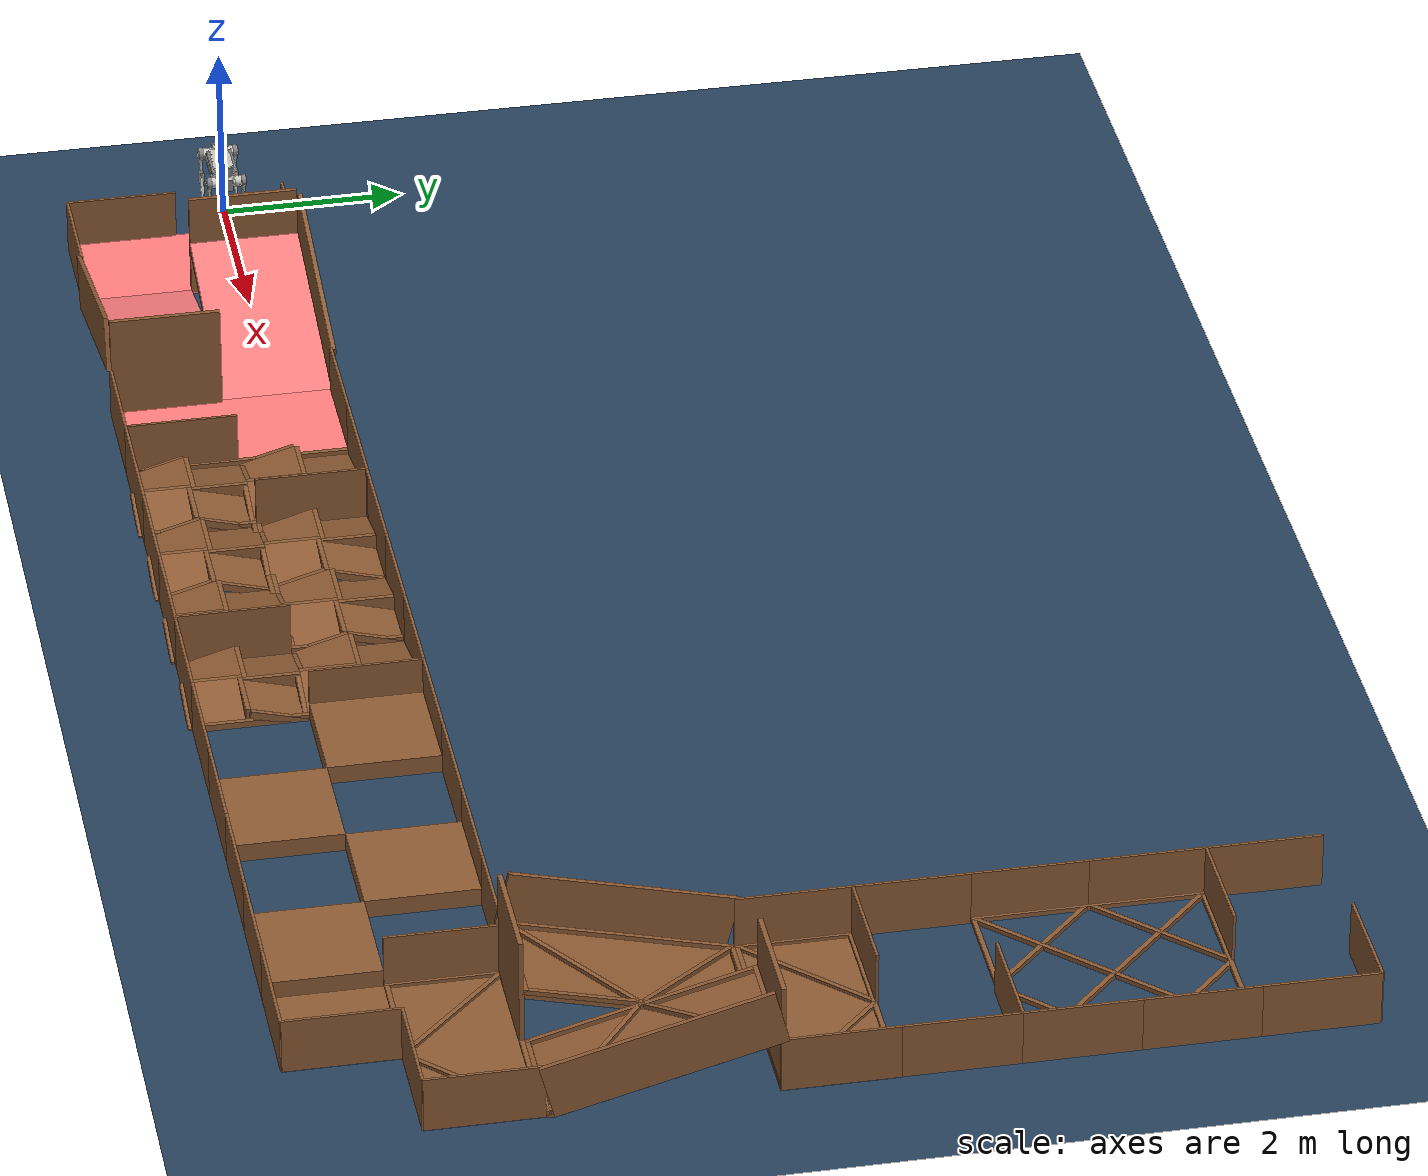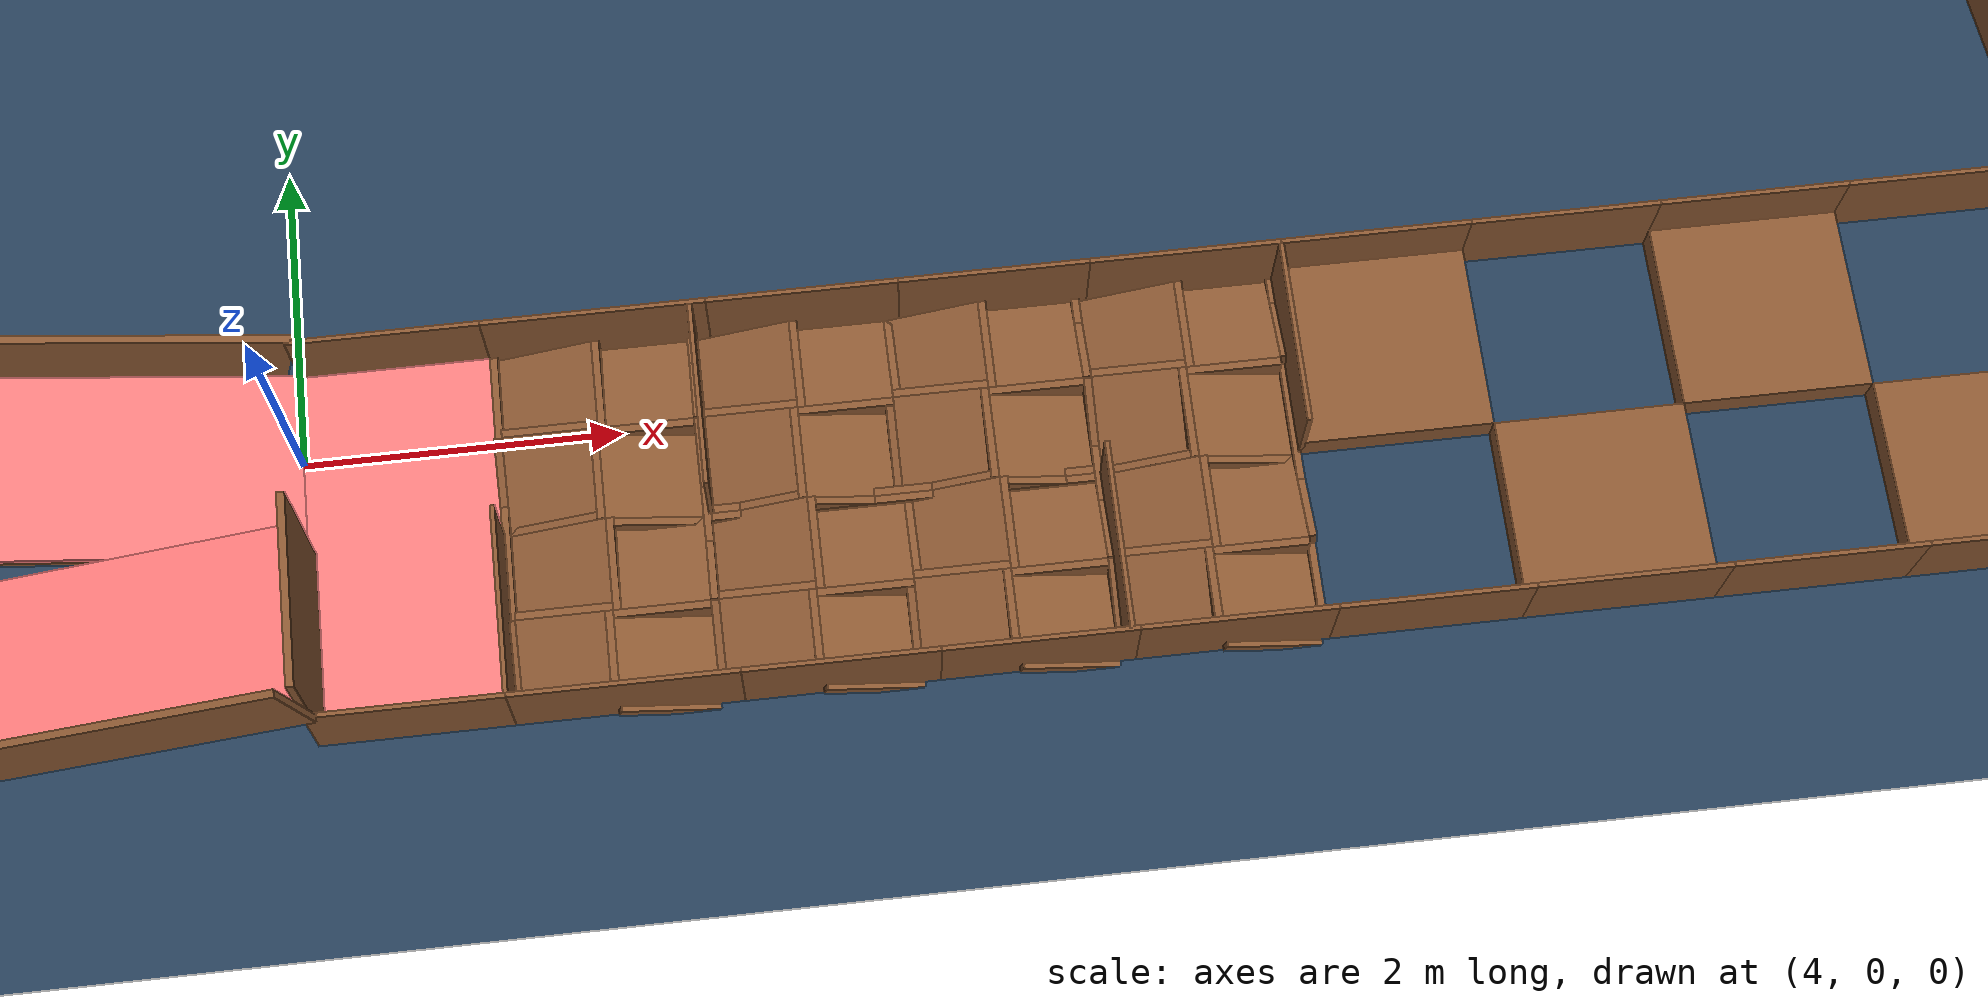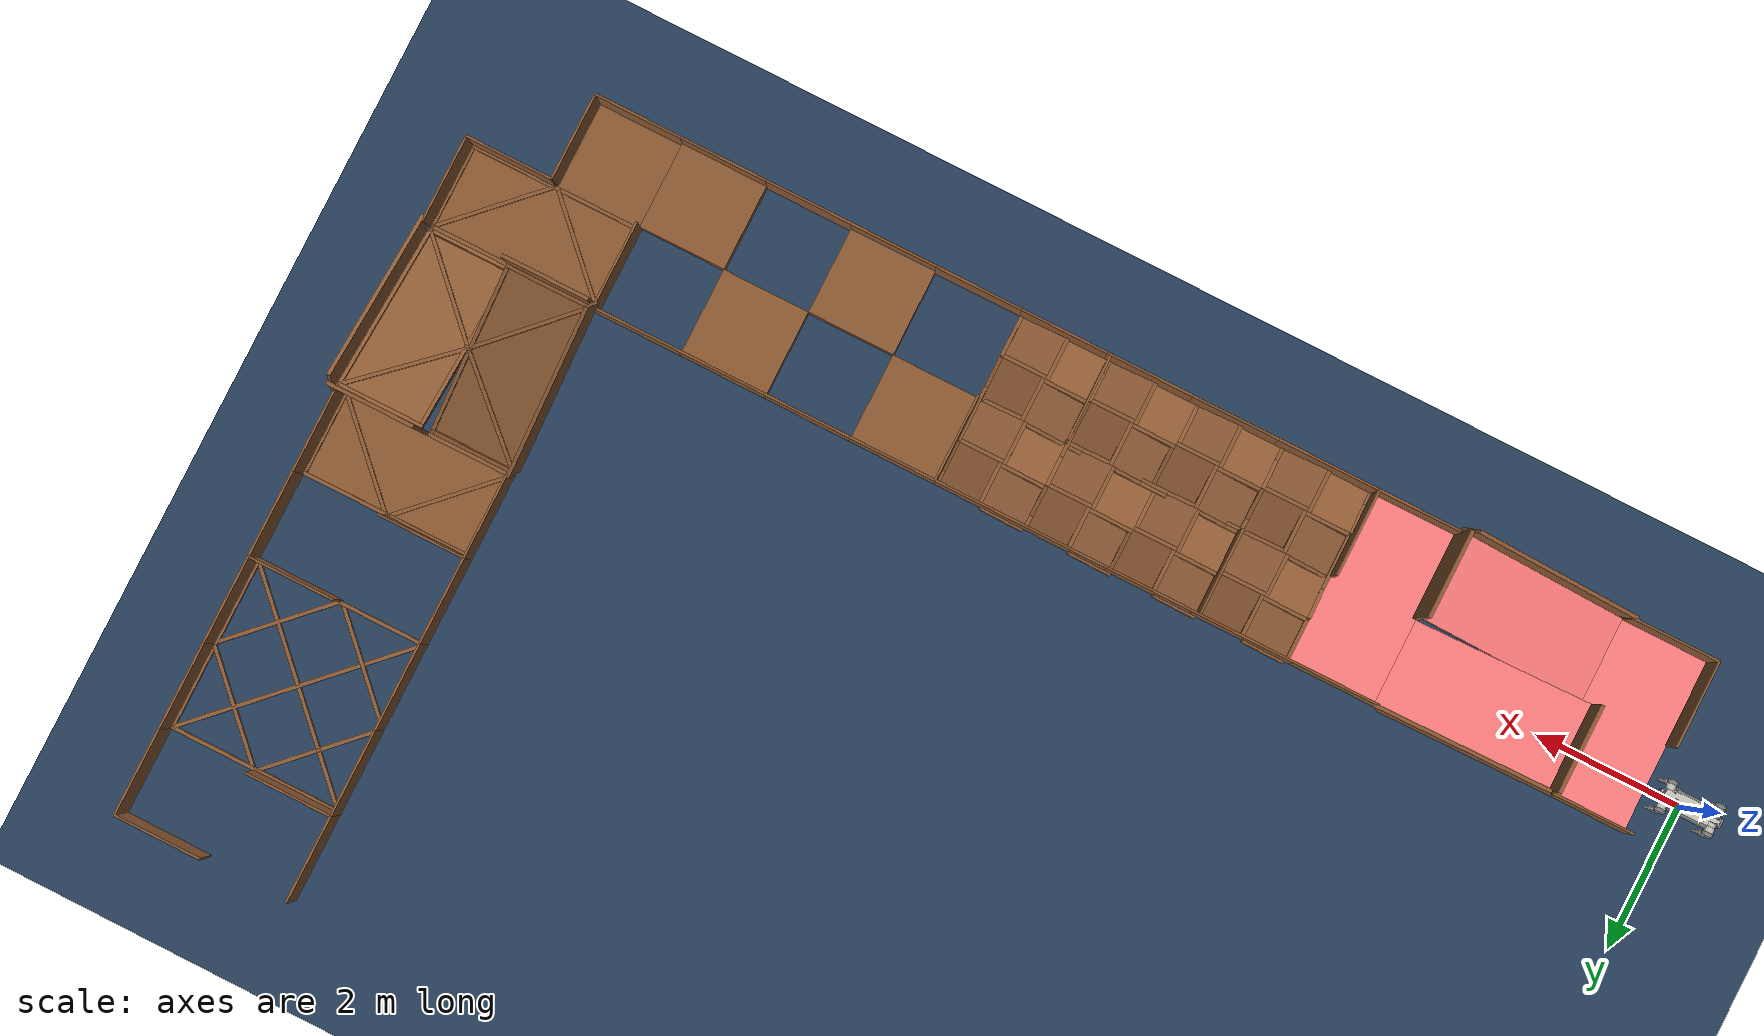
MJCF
<mujoco model="b2 scene">
  <include file="b2.xml"/>

  <statistic center="0 0 0.1" extent="0.8" />

  <visual>
    <headlight diffuse="0.6 0.6 0.6" ambient="0.3 0.3 0.3" specular="0 0 0" />
    <rgba haze="0.15 0.25 0.35 1" />
    <global azimuth="-130" elevation="-20" />
  </visual>

  <asset>
    <texture type="skybox" builtin="gradient" rgb1="0.3 0.5 0.7" rgb2="0 0 0" width="512" height="3072" />
    <texture type="2d" name="groundplane" builtin="checker" mark="edge" rgb1="0.2 0.3 0.4" rgb2="0.1 0.2 0.3" markrgb="0.8 0.8 0.8" width="300" height="300" />
    <material name="groundplane" texture="groundplane" texuniform="true" texrepeat="5 5" reflectance="0.0" />
  <texture name="wood_tex" type="2d" builtin="flat" rgb1="0.55 0.35 0.2" width="512" height="512" /><material name="wood_mat" texture="wood_tex" specular="0.2" shininess="0.1" rgba="1 1 1 1" /><texture name="sponge_tex" type="2d" builtin="flat" rgb1="1.0 0.7 0.7" width="512" height="512" /><material name="mat_sponge" texture="sponge_tex" specular="0.1" shininess="0.1" rgba="1 0.7 0.7 1" /></asset>

  <worldbody>
    <light pos="0 0 1.5" dir="0 0 -1" directional="true" />
    <geom name="floor" size="0 0 0.05" type="plane" material="groundplane" />
  <geom pos="2.833740429450787 2.220446049250313e-16 0.27579632720971" type="box" size="1.1981652640600127 0.6 0.025" quat="6.074277307224726e-17 0.12620041281310998 -7.727546580132487e-18 0.9920047660197004" material="wood_mat" friction="0.5 0.005 0.0001" /><geom pos="1.6550000000000002 2.220446049250313e-16 0.6" type="box" size="0.025 0.6 0.6" quat="6.123233995736766e-17 0.0 0.0 1.0" material="wood_mat" friction="0.5 0.005 0.0001" /><geom pos="2.833740429450787 0.6250000000000002 0.60079632720971" type="box" size="1.1981652640600127 0.025 0.3" quat="6.074277307224726e-17 0.12620041281310998 -7.727546580132487e-18 0.9920047660197004" material="wood_mat" friction="0.5 0.005 0.0001" /><geom pos="2.846259570549213 -1.2 0.27579632720971" type="box" size="1.1981652640600127 0.6 0.025" quat="0.9920047660197004 0.0 -0.12620041281310998 0.0" material="wood_mat" friction="0.5 0.005 0.0001" /><geom pos="4.025 -1.2 0.6" type="box" size="0.025 0.6 0.6" quat="1.0 0.0 0.0 0.0" material="wood_mat" friction="0.5 0.005 0.0001" /><geom pos="2.846259570549213 -1.825 0.60079632720971" type="box" size="1.1981652640600127 0.025 0.3" quat="0.9920047660197004 0.0 -0.12620041281310998 0.0" material="wood_mat" friction="0.5 0.005 0.0001" /><geom pos="4.6 -1.7999999999999998 0.3" type="box" size="0.6 0.3 0.015" quat="0.7071067811865476 0.7071067811865476 0.0 0.0" material="wood_mat" friction="0.5 0.005 0.0001" /><geom pos="1.08 -1.7999999999999998 0.3" type="box" size="0.6 0.3 0.015" quat="0.7071067811865476 0.7071067811865476 0.0 0.0" material="wood_mat" friction="0.5 0.005 0.0001" /><geom pos="4.6 0.6000000000000001 0.3" type="box" size="0.6 0.3 0.015" quat="0.7071067811865476 0.7071067811865476 0.0 0.0" material="wood_mat" friction="0.5 0.005 0.0001" /><geom pos="1.08 0.6000000000000001 0.3" type="box" size="0.6 0.3 0.015" quat="0.7071067811865476 0.7071067811865476 0.0 0.0" material="wood_mat" friction="0.5 0.005 0.0001" /><geom pos="0.48 -1.2 0.3" type="box" size="0.3 0.6 0.015" quat="0.7071067811865476 0.0 0.7071067811865476 0.0" material="wood_mat" friction="0.5 0.005 0.0001" /><geom pos="1.08 -0.6 0.025" type="box" size="0.6 1.2 0.025" quat="1.0 0.0 0.0 0.0" material="mat_sponge" solref="0.03 1" priority="1" solmix="1" friction="1.2 0.005 0.0001" /><geom pos="4.6 -0.6 0.025" type="box" size="0.6 1.2 0.025" quat="1.0 0.0 0.0 0.0" material="mat_sponge" solref="0.03 1" priority="1" solmix="1" friction="1.2 0.005 0.0001" /><geom pos="2.833740429450787 2.220446049250313e-16 0.32579632720970997" type="box" size="1.1981652640600127 0.6 0.025" quat="6.074277307224726e-17 0.12620041281310998 -7.727546580132487e-18 0.9920047660197004" material="mat_sponge" solref="0.03 1" priority="1" solmix="1" friction="1.2 0.005 0.0001" /><geom pos="2.846259570549213 -1.2 0.32579632720970997" type="box" size="1.1981652640600127 0.6 0.025" quat="0.9920047660197004 0.0 -0.12620041281310998 0.0" material="mat_sponge" solref="0.03 1" priority="1" solmix="1" friction="1.2 0.005 0.0001" /><geom pos="5.225 -0.6 0.0" type="box" size="1.2 0.025 0.05" quat="0.7071067811865476 0.0 0.0 0.7071067811865476" material="wood_mat" friction="0.5 0.005 0.0001" /><geom pos="5.55 -1.4934084623528479 0.05788461836407774" type="box" size="0.311004823113726 0.3 0.025" quat="0.7008236699478855 0.09405415270352165 -0.09405415270352165 0.7008236699478855" material="wood_mat" friction="0.5 0.005 0.0001" /><geom pos="5.55 -1.1749999999999998 0.082" type="box" size="0.025 0.3 0.082" quat="0.7071067811865476 0.0 0.0 0.7071067811865476" material="wood_mat" friction="0.5 0.005 0.0001" /><geom pos="5.875 -1.4934084623528479 0.04188461836407773" type="box" size="0.311004823113726 0.025 0.041" quat="0.7008236699478855 0.09405415270352165 -0.09405415270352165 0.7008236699478855" material="wood_mat" friction="0.5 0.005 0.0001" /><geom pos="5.225 -1.4934084623528479 0.04188461836407773" type="box" size="0.311004823113726 0.025 0.041" quat="0.7008236699478855 0.09405415270352165 -0.09405415270352165 0.7008236699478855" material="wood_mat" friction="0.5 0.005 0.0001" /><geom pos="5.556591537647153 -0.8999999999999999 0.05788461836407774" type="box" size="0.311004823113726 0.3 0.025" quat="0.9911143388723852 0.0 -0.1330126583508304 0.0" material="wood_mat" friction="0.5 0.005 0.0001" /><geom pos="5.875 -0.8999999999999999 0.082" type="box" size="0.025 0.3 0.082" quat="1.0 0.0 0.0 0.0" material="wood_mat" friction="0.5 0.005 0.0001" /><geom pos="5.556591537647153 -1.225 0.04188461836407773" type="box" size="0.311004823113726 0.025 0.041" quat="0.9911143388723852 0.0 -0.1330126583508304 0.0" material="wood_mat" friction="0.5 0.005 0.0001" /><geom pos="5.556591537647153 -0.575 0.04188461836407773" type="box" size="0.311004823113726 0.025 0.041" quat="0.9911143388723852 0.0 -0.1330126583508304 0.0" material="wood_mat" friction="0.5 0.005 0.0001" /><geom pos="6.143408462352848 -1.5 0.05788461836407774" type="box" size="0.311004823113726 0.3 0.025" quat="6.068825013445559e-17 0.1330126583508304 -8.144676314771245e-18 0.9911143388723852" material="wood_mat" friction="0.5 0.005 0.0001" /><geom pos="5.825 -1.5 0.082" type="box" size="0.025 0.3 0.082" quat="6.123233995736766e-17 0.0 0.0 1.0" material="wood_mat" friction="0.5 0.005 0.0001" /><geom pos="6.143408462352848 -1.1749999999999998 0.04188461836407773" type="box" size="0.311004823113726 0.025 0.041" quat="6.068825013445559e-17 0.1330126583508304 -8.144676314771245e-18 0.9911143388723852" material="wood_mat" friction="0.5 0.005 0.0001" /><geom pos="6.143408462352848 -1.825 0.04188461836407773" type="box" size="0.311004823113726 0.025 0.041" quat="6.068825013445559e-17 0.1330126583508304 -8.144676314771245e-18 0.9911143388723852" material="wood_mat" friction="0.5 0.005 0.0001" /><geom pos="6.15 -0.9065915376471521 0.05788461836407774" type="box" size="0.311004823113726 0.3 0.025" quat="-0.7008236699478854 0.09405415270352165 0.09405415270352163 0.7008236699478855" material="wood_mat" friction="0.5 0.005 0.0001" /><geom pos="6.15 -1.225 0.082" type="box" size="0.025 0.3 0.082" quat="-0.7071067811865475 -0.0 0.0 0.7071067811865476" material="wood_mat" friction="0.5 0.005 0.0001" /><geom pos="5.824999999999999 -0.9065915376471521 0.04188461836407773" type="box" size="0.311004823113726 0.025 0.041" quat="-0.7008236699478854 0.09405415270352165 0.09405415270352163 0.7008236699478855" material="wood_mat" friction="0.5 0.005 0.0001" /><geom pos="6.475 -0.9065915376471521 0.04188461836407773" type="box" size="0.311004823113726 0.025 0.041" quat="-0.7008236699478854 0.09405415270352165 0.09405415270352163 0.7008236699478855" material="wood_mat" friction="0.5 0.005 0.0001" /><geom pos="5.55 -0.2934084623528479 0.05788461836407774" type="box" size="0.311004823113726 0.3 0.025" quat="0.7008236699478855 0.09405415270352165 -0.09405415270352165 0.7008236699478855" material="wood_mat" friction="0.5 0.005 0.0001" /><geom pos="5.55 0.025000000000000133 0.082" type="box" size="0.025 0.3 0.082" quat="0.7071067811865476 0.0 0.0 0.7071067811865476" material="wood_mat" friction="0.5 0.005 0.0001" /><geom pos="5.875 -0.2934084623528479 0.04188461836407773" type="box" size="0.311004823113726 0.025 0.041" quat="0.7008236699478855 0.09405415270352165 -0.09405415270352165 0.7008236699478855" material="wood_mat" friction="0.5 0.005 0.0001" /><geom pos="5.225 -0.2934084623528479 0.04188461836407773" type="box" size="0.311004823113726 0.025 0.041" quat="0.7008236699478855 0.09405415270352165 -0.09405415270352165 0.7008236699478855" material="wood_mat" friction="0.5 0.005 0.0001" /><geom pos="5.556591537647153 0.30000000000000004 0.05788461836407774" type="box" size="0.311004823113726 0.3 0.025" quat="0.9911143388723852 0.0 -0.1330126583508304 0.0" material="wood_mat" friction="0.5 0.005 0.0001" /><geom pos="5.875 0.30000000000000004 0.082" type="box" size="0.025 0.3 0.082" quat="1.0 0.0 0.0 0.0" material="wood_mat" friction="0.5 0.005 0.0001" /><geom pos="5.556591537647153 -0.02499999999999991 0.04188461836407773" type="box" size="0.311004823113726 0.025 0.041" quat="0.9911143388723852 0.0 -0.1330126583508304 0.0" material="wood_mat" friction="0.5 0.005 0.0001" /><geom pos="5.556591537647153 0.625 0.04188461836407773" type="box" size="0.311004823113726 0.025 0.041" quat="0.9911143388723852 0.0 -0.1330126583508304 0.0" material="wood_mat" friction="0.5 0.005 0.0001" /><geom pos="6.143408462352848 -0.30000000000000004 0.05788461836407774" type="box" size="0.311004823113726 0.3 0.025" quat="6.068825013445559e-17 0.1330126583508304 -8.144676314771245e-18 0.9911143388723852" material="wood_mat" friction="0.5 0.005 0.0001" /><geom pos="5.825 -0.29999999999999993 0.082" type="box" size="0.025 0.3 0.082" quat="6.123233995736766e-17 0.0 0.0 1.0" material="wood_mat" friction="0.5 0.005 0.0001" /><geom pos="6.143408462352848 0.025000000000000133 0.04188461836407773" type="box" size="0.311004823113726 0.025 0.041" quat="6.068825013445559e-17 0.1330126583508304 -8.144676314771245e-18 0.9911143388723852" material="wood_mat" friction="0.5 0.005 0.0001" /><geom pos="6.143408462352848 -0.625 0.04188461836407773" type="box" size="0.311004823113726 0.025 0.041" quat="6.068825013445559e-17 0.1330126583508304 -8.144676314771245e-18 0.9911143388723852" material="wood_mat" friction="0.5 0.005 0.0001" /><geom pos="6.15 0.2934084623528477 0.05788461836407774" type="box" size="0.311004823113726 0.3 0.025" quat="-0.7008236699478854 0.09405415270352165 0.09405415270352163 0.7008236699478855" material="wood_mat" friction="0.5 0.005 0.0001" /><geom pos="6.15 -0.025000000000000133 0.082" type="box" size="0.025 0.3 0.082" quat="-0.7071067811865475 -0.0 0.0 0.7071067811865476" material="wood_mat" friction="0.5 0.005 0.0001" /><geom pos="5.824999999999999 0.2934084623528479 0.04188461836407773" type="box" size="0.311004823113726 0.025 0.041" quat="-0.7008236699478854 0.09405415270352165 0.09405415270352163 0.7008236699478855" material="wood_mat" friction="0.5 0.005 0.0001" /><geom pos="6.475 0.2934084623528477 0.04188461836407773" type="box" size="0.311004823113726 0.025 0.041" quat="-0.7008236699478854 0.09405415270352165 0.09405415270352163 0.7008236699478855" material="wood_mat" friction="0.5 0.005 0.0001" /><geom pos="6.475 -0.6 0.0" type="box" size="1.2 0.025 0.05" quat="0.7071067811865476 0.0 0.0 0.7071067811865476" material="wood_mat" friction="0.5 0.005 0.0001" /><geom pos="6.800000000000001 -1.4934084623528479 0.05788461836407774" type="box" size="0.311004823113726 0.3 0.025" quat="0.7008236699478855 0.09405415270352165 -0.09405415270352165 0.7008236699478855" material="wood_mat" friction="0.5 0.005 0.0001" /><geom pos="6.800000000000001 -1.1749999999999998 0.082" type="box" size="0.025 0.3 0.082" quat="0.7071067811865476 0.0 0.0 0.7071067811865476" material="wood_mat" friction="0.5 0.005 0.0001" /><geom pos="7.125 -1.4934084623528479 0.04188461836407773" type="box" size="0.311004823113726 0.025 0.041" quat="0.7008236699478855 0.09405415270352165 -0.09405415270352165 0.7008236699478855" material="wood_mat" friction="0.5 0.005 0.0001" /><geom pos="6.475 -1.4934084623528479 0.04188461836407773" type="box" size="0.311004823113726 0.025 0.041" quat="0.7008236699478855 0.09405415270352165 -0.09405415270352165 0.7008236699478855" material="wood_mat" friction="0.5 0.005 0.0001" /><geom pos="6.806591537647153 -0.8999999999999999 0.05788461836407774" type="box" size="0.311004823113726 0.3 0.025" quat="0.9911143388723852 0.0 -0.1330126583508304 0.0" material="wood_mat" friction="0.5 0.005 0.0001" /><geom pos="7.125 -0.8999999999999999 0.082" type="box" size="0.025 0.3 0.082" quat="1.0 0.0 0.0 0.0" material="wood_mat" friction="0.5 0.005 0.0001" /><geom pos="6.806591537647153 -1.225 0.04188461836407773" type="box" size="0.311004823113726 0.025 0.041" quat="0.9911143388723852 0.0 -0.1330126583508304 0.0" material="wood_mat" friction="0.5 0.005 0.0001" /><geom pos="6.806591537647153 -0.575 0.04188461836407773" type="box" size="0.311004823113726 0.025 0.041" quat="0.9911143388723852 0.0 -0.1330126583508304 0.0" material="wood_mat" friction="0.5 0.005 0.0001" /><geom pos="7.393408462352848 -1.5 0.05788461836407774" type="box" size="0.311004823113726 0.3 0.025" quat="6.068825013445559e-17 0.1330126583508304 -8.144676314771245e-18 0.9911143388723852" material="wood_mat" friction="0.5 0.005 0.0001" /><geom pos="7.075 -1.5 0.082" type="box" size="0.025 0.3 0.082" quat="6.123233995736766e-17 0.0 0.0 1.0" material="wood_mat" friction="0.5 0.005 0.0001" /><geom pos="7.393408462352848 -1.1749999999999998 0.04188461836407773" type="box" size="0.311004823113726 0.025 0.041" quat="6.068825013445559e-17 0.1330126583508304 -8.144676314771245e-18 0.9911143388723852" material="wood_mat" friction="0.5 0.005 0.0001" /><geom pos="7.393408462352848 -1.825 0.04188461836407773" type="box" size="0.311004823113726 0.025 0.041" quat="6.068825013445559e-17 0.1330126583508304 -8.144676314771245e-18 0.9911143388723852" material="wood_mat" friction="0.5 0.005 0.0001" /><geom pos="7.4 -0.9065915376471521 0.05788461836407774" type="box" size="0.311004823113726 0.3 0.025" quat="-0.7008236699478854 0.09405415270352165 0.09405415270352163 0.7008236699478855" material="wood_mat" friction="0.5 0.005 0.0001" /><geom pos="7.4 -1.225 0.082" type="box" size="0.025 0.3 0.082" quat="-0.7071067811865475 -0.0 0.0 0.7071067811865476" material="wood_mat" friction="0.5 0.005 0.0001" /><geom pos="7.074999999999999 -0.9065915376471521 0.04188461836407773" type="box" size="0.311004823113726 0.025 0.041" quat="-0.7008236699478854 0.09405415270352165 0.09405415270352163 0.7008236699478855" material="wood_mat" friction="0.5 0.005 0.0001" /><geom pos="7.725 -0.9065915376471521 0.04188461836407773" type="box" size="0.311004823113726 0.025 0.041" quat="-0.7008236699478854 0.09405415270352165 0.09405415270352163 0.7008236699478855" material="wood_mat" friction="0.5 0.005 0.0001" /><geom pos="6.800000000000001 -0.2934084623528479 0.05788461836407774" type="box" size="0.311004823113726 0.3 0.025" quat="0.7008236699478855 0.09405415270352165 -0.09405415270352165 0.7008236699478855" material="wood_mat" friction="0.5 0.005 0.0001" /><geom pos="6.800000000000001 0.025000000000000133 0.082" type="box" size="0.025 0.3 0.082" quat="0.7071067811865476 0.0 0.0 0.7071067811865476" material="wood_mat" friction="0.5 0.005 0.0001" /><geom pos="7.125 -0.2934084623528479 0.04188461836407773" type="box" size="0.311004823113726 0.025 0.041" quat="0.7008236699478855 0.09405415270352165 -0.09405415270352165 0.7008236699478855" material="wood_mat" friction="0.5 0.005 0.0001" /><geom pos="6.475 -0.2934084623528479 0.04188461836407773" type="box" size="0.311004823113726 0.025 0.041" quat="0.7008236699478855 0.09405415270352165 -0.09405415270352165 0.7008236699478855" material="wood_mat" friction="0.5 0.005 0.0001" /><geom pos="6.806591537647153 0.30000000000000004 0.05788461836407774" type="box" size="0.311004823113726 0.3 0.025" quat="0.9911143388723852 0.0 -0.1330126583508304 0.0" material="wood_mat" friction="0.5 0.005 0.0001" /><geom pos="7.125 0.30000000000000004 0.082" type="box" size="0.025 0.3 0.082" quat="1.0 0.0 0.0 0.0" material="wood_mat" friction="0.5 0.005 0.0001" /><geom pos="6.806591537647153 -0.02499999999999991 0.04188461836407773" type="box" size="0.311004823113726 0.025 0.041" quat="0.9911143388723852 0.0 -0.1330126583508304 0.0" material="wood_mat" friction="0.5 0.005 0.0001" /><geom pos="6.806591537647153 0.625 0.04188461836407773" type="box" size="0.311004823113726 0.025 0.041" quat="0.9911143388723852 0.0 -0.1330126583508304 0.0" material="wood_mat" friction="0.5 0.005 0.0001" /><geom pos="7.393408462352848 -0.30000000000000004 0.05788461836407774" type="box" size="0.311004823113726 0.3 0.025" quat="6.068825013445559e-17 0.1330126583508304 -8.144676314771245e-18 0.9911143388723852" material="wood_mat" friction="0.5 0.005 0.0001" /><geom pos="7.075 -0.29999999999999993 0.082" type="box" size="0.025 0.3 0.082" quat="6.123233995736766e-17 0.0 0.0 1.0" material="wood_mat" friction="0.5 0.005 0.0001" /><geom pos="7.393408462352848 0.025000000000000133 0.04188461836407773" type="box" size="0.311004823113726 0.025 0.041" quat="6.068825013445559e-17 0.1330126583508304 -8.144676314771245e-18 0.9911143388723852" material="wood_mat" friction="0.5 0.005 0.0001" /><geom pos="7.393408462352848 -0.625 0.04188461836407773" type="box" size="0.311004823113726 0.025 0.041" quat="6.068825013445559e-17 0.1330126583508304 -8.144676314771245e-18 0.9911143388723852" material="wood_mat" friction="0.5 0.005 0.0001" /><geom pos="7.4 0.2934084623528477 0.05788461836407774" type="box" size="0.311004823113726 0.3 0.025" quat="-0.7008236699478854 0.09405415270352165 0.09405415270352163 0.7008236699478855" material="wood_mat" friction="0.5 0.005 0.0001" /><geom pos="7.4 -0.025000000000000133 0.082" type="box" size="0.025 0.3 0.082" quat="-0.7071067811865475 -0.0 0.0 0.7071067811865476" material="wood_mat" friction="0.5 0.005 0.0001" /><geom pos="7.074999999999999 0.2934084623528479 0.04188461836407773" type="box" size="0.311004823113726 0.025 0.041" quat="-0.7008236699478854 0.09405415270352165 0.09405415270352163 0.7008236699478855" material="wood_mat" friction="0.5 0.005 0.0001" /><geom pos="7.725 0.2934084623528477 0.04188461836407773" type="box" size="0.311004823113726 0.025 0.041" quat="-0.7008236699478854 0.09405415270352165 0.09405415270352163 0.7008236699478855" material="wood_mat" friction="0.5 0.005 0.0001" /><geom pos="8.0 -1.4934084623528479 0.05788461836407774" type="box" size="0.311004823113726 0.3 0.025" quat="0.7008236699478855 0.09405415270352165 -0.09405415270352165 0.7008236699478855" material="wood_mat" friction="0.5 0.005 0.0001" /><geom pos="8.0 -1.1749999999999998 0.082" type="box" size="0.025 0.3 0.082" quat="0.7071067811865476 0.0 0.0 0.7071067811865476" material="wood_mat" friction="0.5 0.005 0.0001" /><geom pos="8.325 -1.4934084623528479 0.04188461836407773" type="box" size="0.311004823113726 0.025 0.041" quat="0.7008236699478855 0.09405415270352165 -0.09405415270352165 0.7008236699478855" material="wood_mat" friction="0.5 0.005 0.0001" /><geom pos="7.675 -1.4934084623528479 0.04188461836407773" type="box" size="0.311004823113726 0.025 0.041" quat="0.7008236699478855 0.09405415270352165 -0.09405415270352165 0.7008236699478855" material="wood_mat" friction="0.5 0.005 0.0001" /><geom pos="8.006591537647152 -0.8999999999999999 0.05788461836407774" type="box" size="0.311004823113726 0.3 0.025" quat="0.9911143388723852 0.0 -0.1330126583508304 0.0" material="wood_mat" friction="0.5 0.005 0.0001" /><geom pos="8.325 -0.8999999999999999 0.082" type="box" size="0.025 0.3 0.082" quat="1.0 0.0 0.0 0.0" material="wood_mat" friction="0.5 0.005 0.0001" /><geom pos="8.006591537647152 -1.225 0.04188461836407773" type="box" size="0.311004823113726 0.025 0.041" quat="0.9911143388723852 0.0 -0.1330126583508304 0.0" material="wood_mat" friction="0.5 0.005 0.0001" /><geom pos="8.006591537647152 -0.575 0.04188461836407773" type="box" size="0.311004823113726 0.025 0.041" quat="0.9911143388723852 0.0 -0.1330126583508304 0.0" material="wood_mat" friction="0.5 0.005 0.0001" /><geom pos="8.593408462352848 -1.5 0.05788461836407774" type="box" size="0.311004823113726 0.3 0.025" quat="6.068825013445559e-17 0.1330126583508304 -8.144676314771245e-18 0.9911143388723852" material="wood_mat" friction="0.5 0.005 0.0001" /><geom pos="8.274999999999999 -1.5 0.082" type="box" size="0.025 0.3 0.082" quat="6.123233995736766e-17 0.0 0.0 1.0" material="wood_mat" friction="0.5 0.005 0.0001" /><geom pos="8.593408462352848 -1.1749999999999998 0.04188461836407773" type="box" size="0.311004823113726 0.025 0.041" quat="6.068825013445559e-17 0.1330126583508304 -8.144676314771245e-18 0.9911143388723852" material="wood_mat" friction="0.5 0.005 0.0001" /><geom pos="8.593408462352848 -1.825 0.04188461836407773" type="box" size="0.311004823113726 0.025 0.041" quat="6.068825013445559e-17 0.1330126583508304 -8.144676314771245e-18 0.9911143388723852" material="wood_mat" friction="0.5 0.005 0.0001" /><geom pos="8.6 -0.9065915376471521 0.05788461836407774" type="box" size="0.311004823113726 0.3 0.025" quat="-0.7008236699478854 0.09405415270352165 0.09405415270352163 0.7008236699478855" material="wood_mat" friction="0.5 0.005 0.0001" /><geom pos="8.6 -1.225 0.082" type="box" size="0.025 0.3 0.082" quat="-0.7071067811865475 -0.0 0.0 0.7071067811865476" material="wood_mat" friction="0.5 0.005 0.0001" /><geom pos="8.274999999999999 -0.9065915376471521 0.04188461836407773" type="box" size="0.311004823113726 0.025 0.041" quat="-0.7008236699478854 0.09405415270352165 0.09405415270352163 0.7008236699478855" material="wood_mat" friction="0.5 0.005 0.0001" /><geom pos="8.925 -0.9065915376471521 0.04188461836407773" type="box" size="0.311004823113726 0.025 0.041" quat="-0.7008236699478854 0.09405415270352165 0.09405415270352163 0.7008236699478855" material="wood_mat" friction="0.5 0.005 0.0001" /><geom pos="8.0 -0.2934084623528479 0.05788461836407774" type="box" size="0.311004823113726 0.3 0.025" quat="0.7008236699478855 0.09405415270352165 -0.09405415270352165 0.7008236699478855" material="wood_mat" friction="0.5 0.005 0.0001" /><geom pos="8.0 0.025000000000000133 0.082" type="box" size="0.025 0.3 0.082" quat="0.7071067811865476 0.0 0.0 0.7071067811865476" material="wood_mat" friction="0.5 0.005 0.0001" /><geom pos="8.325 -0.2934084623528479 0.04188461836407773" type="box" size="0.311004823113726 0.025 0.041" quat="0.7008236699478855 0.09405415270352165 -0.09405415270352165 0.7008236699478855" material="wood_mat" friction="0.5 0.005 0.0001" /><geom pos="7.675 -0.2934084623528479 0.04188461836407773" type="box" size="0.311004823113726 0.025 0.041" quat="0.7008236699478855 0.09405415270352165 -0.09405415270352165 0.7008236699478855" material="wood_mat" friction="0.5 0.005 0.0001" /><geom pos="8.006591537647152 0.30000000000000004 0.05788461836407774" type="box" size="0.311004823113726 0.3 0.025" quat="0.9911143388723852 0.0 -0.1330126583508304 0.0" material="wood_mat" friction="0.5 0.005 0.0001" /><geom pos="8.325 0.30000000000000004 0.082" type="box" size="0.025 0.3 0.082" quat="1.0 0.0 0.0 0.0" material="wood_mat" friction="0.5 0.005 0.0001" /><geom pos="8.006591537647152 -0.02499999999999991 0.04188461836407773" type="box" size="0.311004823113726 0.025 0.041" quat="0.9911143388723852 0.0 -0.1330126583508304 0.0" material="wood_mat" friction="0.5 0.005 0.0001" /><geom pos="8.006591537647152 0.625 0.04188461836407773" type="box" size="0.311004823113726 0.025 0.041" quat="0.9911143388723852 0.0 -0.1330126583508304 0.0" material="wood_mat" friction="0.5 0.005 0.0001" /><geom pos="8.593408462352848 -0.30000000000000004 0.05788461836407774" type="box" size="0.311004823113726 0.3 0.025" quat="6.068825013445559e-17 0.1330126583508304 -8.144676314771245e-18 0.9911143388723852" material="wood_mat" friction="0.5 0.005 0.0001" /><geom pos="8.274999999999999 -0.29999999999999993 0.082" type="box" size="0.025 0.3 0.082" quat="6.123233995736766e-17 0.0 0.0 1.0" material="wood_mat" friction="0.5 0.005 0.0001" /><geom pos="8.593408462352848 0.025000000000000133 0.04188461836407773" type="box" size="0.311004823113726 0.025 0.041" quat="6.068825013445559e-17 0.1330126583508304 -8.144676314771245e-18 0.9911143388723852" material="wood_mat" friction="0.5 0.005 0.0001" /><geom pos="8.593408462352848 -0.625 0.04188461836407773" type="box" size="0.311004823113726 0.025 0.041" quat="6.068825013445559e-17 0.1330126583508304 -8.144676314771245e-18 0.9911143388723852" material="wood_mat" friction="0.5 0.005 0.0001" /><geom pos="8.6 0.2934084623528477 0.05788461836407774" type="box" size="0.311004823113726 0.3 0.025" quat="-0.7008236699478854 0.09405415270352165 0.09405415270352163 0.7008236699478855" material="wood_mat" friction="0.5 0.005 0.0001" /><geom pos="8.6 -0.025000000000000133 0.082" type="box" size="0.025 0.3 0.082" quat="-0.7071067811865475 -0.0 0.0 0.7071067811865476" material="wood_mat" friction="0.5 0.005 0.0001" /><geom pos="8.274999999999999 0.2934084623528479 0.04188461836407773" type="box" size="0.311004823113726 0.025 0.041" quat="-0.7008236699478854 0.09405415270352165 0.09405415270352163 0.7008236699478855" material="wood_mat" friction="0.5 0.005 0.0001" /><geom pos="8.925 0.2934084623528477 0.04188461836407773" type="box" size="0.311004823113726 0.025 0.041" quat="-0.7008236699478854 0.09405415270352165 0.09405415270352163 0.7008236699478855" material="wood_mat" friction="0.5 0.005 0.0001" /><geom pos="7.7 -0.625 0.0" type="box" size="1.2 0.025 0.05" quat="1.0 0.0 0.0 0.0" material="wood_mat" friction="0.5 0.005 0.0001" /><geom pos="7.7 -0.575 0.0" type="box" size="1.2 0.025 0.05" quat="1.0 0.0 0.0 0.0" material="wood_mat" friction="0.5 0.005 0.0001" /><geom pos="8.925 -0.6 0.0" type="box" size="1.2 0.025 0.05" quat="0.7071067811865476 0.0 0.0 0.7071067811865476" material="wood_mat" friction="0.5 0.005 0.0001" /><geom pos="9.25 -1.4934084623528479 0.05788461836407774" type="box" size="0.311004823113726 0.3 0.025" quat="0.7008236699478855 0.09405415270352165 -0.09405415270352165 0.7008236699478855" material="wood_mat" friction="0.5 0.005 0.0001" /><geom pos="9.25 -1.1749999999999998 0.082" type="box" size="0.025 0.3 0.082" quat="0.7071067811865476 0.0 0.0 0.7071067811865476" material="wood_mat" friction="0.5 0.005 0.0001" /><geom pos="9.575 -1.4934084623528479 0.04188461836407773" type="box" size="0.311004823113726 0.025 0.041" quat="0.7008236699478855 0.09405415270352165 -0.09405415270352165 0.7008236699478855" material="wood_mat" friction="0.5 0.005 0.0001" /><geom pos="8.925 -1.4934084623528479 0.04188461836407773" type="box" size="0.311004823113726 0.025 0.041" quat="0.7008236699478855 0.09405415270352165 -0.09405415270352165 0.7008236699478855" material="wood_mat" friction="0.5 0.005 0.0001" /><geom pos="9.256591537647152 -0.8999999999999999 0.05788461836407774" type="box" size="0.311004823113726 0.3 0.025" quat="0.9911143388723852 0.0 -0.1330126583508304 0.0" material="wood_mat" friction="0.5 0.005 0.0001" /><geom pos="9.575 -0.8999999999999999 0.082" type="box" size="0.025 0.3 0.082" quat="1.0 0.0 0.0 0.0" material="wood_mat" friction="0.5 0.005 0.0001" /><geom pos="9.256591537647152 -1.225 0.04188461836407773" type="box" size="0.311004823113726 0.025 0.041" quat="0.9911143388723852 0.0 -0.1330126583508304 0.0" material="wood_mat" friction="0.5 0.005 0.0001" /><geom pos="9.256591537647152 -0.575 0.04188461836407773" type="box" size="0.311004823113726 0.025 0.041" quat="0.9911143388723852 0.0 -0.1330126583508304 0.0" material="wood_mat" friction="0.5 0.005 0.0001" /><geom pos="9.843408462352848 -1.5 0.05788461836407774" type="box" size="0.311004823113726 0.3 0.025" quat="6.068825013445559e-17 0.1330126583508304 -8.144676314771245e-18 0.9911143388723852" material="wood_mat" friction="0.5 0.005 0.0001" /><geom pos="9.524999999999999 -1.5 0.082" type="box" size="0.025 0.3 0.082" quat="6.123233995736766e-17 0.0 0.0 1.0" material="wood_mat" friction="0.5 0.005 0.0001" /><geom pos="9.843408462352848 -1.1749999999999998 0.04188461836407773" type="box" size="0.311004823113726 0.025 0.041" quat="6.068825013445559e-17 0.1330126583508304 -8.144676314771245e-18 0.9911143388723852" material="wood_mat" friction="0.5 0.005 0.0001" /><geom pos="9.843408462352848 -1.825 0.04188461836407773" type="box" size="0.311004823113726 0.025 0.041" quat="6.068825013445559e-17 0.1330126583508304 -8.144676314771245e-18 0.9911143388723852" material="wood_mat" friction="0.5 0.005 0.0001" /><geom pos="9.85 -0.9065915376471521 0.05788461836407774" type="box" size="0.311004823113726 0.3 0.025" quat="-0.7008236699478854 0.09405415270352165 0.09405415270352163 0.7008236699478855" material="wood_mat" friction="0.5 0.005 0.0001" /><geom pos="9.85 -1.225 0.082" type="box" size="0.025 0.3 0.082" quat="-0.7071067811865475 -0.0 0.0 0.7071067811865476" material="wood_mat" friction="0.5 0.005 0.0001" /><geom pos="9.524999999999999 -0.9065915376471521 0.04188461836407773" type="box" size="0.311004823113726 0.025 0.041" quat="-0.7008236699478854 0.09405415270352165 0.09405415270352163 0.7008236699478855" material="wood_mat" friction="0.5 0.005 0.0001" /><geom pos="10.175 -0.9065915376471521 0.04188461836407773" type="box" size="0.311004823113726 0.025 0.041" quat="-0.7008236699478854 0.09405415270352165 0.09405415270352163 0.7008236699478855" material="wood_mat" friction="0.5 0.005 0.0001" /><geom pos="9.25 -0.2934084623528479 0.05788461836407774" type="box" size="0.311004823113726 0.3 0.025" quat="0.7008236699478855 0.09405415270352165 -0.09405415270352165 0.7008236699478855" material="wood_mat" friction="0.5 0.005 0.0001" /><geom pos="9.25 0.025000000000000133 0.082" type="box" size="0.025 0.3 0.082" quat="0.7071067811865476 0.0 0.0 0.7071067811865476" material="wood_mat" friction="0.5 0.005 0.0001" /><geom pos="9.575 -0.2934084623528479 0.04188461836407773" type="box" size="0.311004823113726 0.025 0.041" quat="0.7008236699478855 0.09405415270352165 -0.09405415270352165 0.7008236699478855" material="wood_mat" friction="0.5 0.005 0.0001" /><geom pos="8.925 -0.2934084623528479 0.04188461836407773" type="box" size="0.311004823113726 0.025 0.041" quat="0.7008236699478855 0.09405415270352165 -0.09405415270352165 0.7008236699478855" material="wood_mat" friction="0.5 0.005 0.0001" /><geom pos="9.256591537647152 0.30000000000000004 0.05788461836407774" type="box" size="0.311004823113726 0.3 0.025" quat="0.9911143388723852 0.0 -0.1330126583508304 0.0" material="wood_mat" friction="0.5 0.005 0.0001" /><geom pos="9.575 0.30000000000000004 0.082" type="box" size="0.025 0.3 0.082" quat="1.0 0.0 0.0 0.0" material="wood_mat" friction="0.5 0.005 0.0001" /><geom pos="9.256591537647152 -0.02499999999999991 0.04188461836407773" type="box" size="0.311004823113726 0.025 0.041" quat="0.9911143388723852 0.0 -0.1330126583508304 0.0" material="wood_mat" friction="0.5 0.005 0.0001" /><geom pos="9.256591537647152 0.625 0.04188461836407773" type="box" size="0.311004823113726 0.025 0.041" quat="0.9911143388723852 0.0 -0.1330126583508304 0.0" material="wood_mat" friction="0.5 0.005 0.0001" /><geom pos="9.843408462352848 -0.30000000000000004 0.05788461836407774" type="box" size="0.311004823113726 0.3 0.025" quat="6.068825013445559e-17 0.1330126583508304 -8.144676314771245e-18 0.9911143388723852" material="wood_mat" friction="0.5 0.005 0.0001" /><geom pos="9.524999999999999 -0.29999999999999993 0.082" type="box" size="0.025 0.3 0.082" quat="6.123233995736766e-17 0.0 0.0 1.0" material="wood_mat" friction="0.5 0.005 0.0001" /><geom pos="9.843408462352848 0.025000000000000133 0.04188461836407773" type="box" size="0.311004823113726 0.025 0.041" quat="6.068825013445559e-17 0.1330126583508304 -8.144676314771245e-18 0.9911143388723852" material="wood_mat" friction="0.5 0.005 0.0001" /><geom pos="9.843408462352848 -0.625 0.04188461836407773" type="box" size="0.311004823113726 0.025 0.041" quat="6.068825013445559e-17 0.1330126583508304 -8.144676314771245e-18 0.9911143388723852" material="wood_mat" friction="0.5 0.005 0.0001" /><geom pos="9.85 0.2934084623528477 0.05788461836407774" type="box" size="0.311004823113726 0.3 0.025" quat="-0.7008236699478854 0.09405415270352165 0.09405415270352163 0.7008236699478855" material="wood_mat" friction="0.5 0.005 0.0001" /><geom pos="9.85 -0.025000000000000133 0.082" type="box" size="0.025 0.3 0.082" quat="-0.7071067811865475 -0.0 0.0 0.7071067811865476" material="wood_mat" friction="0.5 0.005 0.0001" /><geom pos="9.524999999999999 0.2934084623528479 0.04188461836407773" type="box" size="0.311004823113726 0.025 0.041" quat="-0.7008236699478854 0.09405415270352165 0.09405415270352163 0.7008236699478855" material="wood_mat" friction="0.5 0.005 0.0001" /><geom pos="10.175 0.2934084623528477 0.04188461836407773" type="box" size="0.311004823113726 0.025 0.041" quat="-0.7008236699478854 0.09405415270352165 0.09405415270352163 0.7008236699478855" material="wood_mat" friction="0.5 0.005 0.0001" /><geom pos="10.175 -0.6 0.0" type="box" size="1.2 0.025 0.05" quat="0.7071067811865476 0.0 0.0 0.7071067811865476" material="wood_mat" friction="0.5 0.005 0.0001" /><geom pos="5.9 0.6000000000000001 0.3" type="box" size="0.7 0.3 0.015" quat="0.7071067811865476 0.7071067811865476 0.0 0.0" material="wood_mat" friction="0.5 0.005 0.0001" /><geom pos="7.2 0.6000000000000001 0.3" type="box" size="0.6 0.3 0.015" quat="0.7071067811865476 0.7071067811865476 0.0 0.0" material="wood_mat" friction="0.5 0.005 0.0001" /><geom pos="8.4 0.6000000000000001 0.3" type="box" size="0.6 0.3 0.015" quat="0.7071067811865476 0.7071067811865476 0.0 0.0" material="wood_mat" friction="0.5 0.005 0.0001" /><geom pos="9.6 0.6000000000000001 0.3" type="box" size="0.6 0.3 0.015" quat="0.7071067811865476 0.7071067811865476 0.0 0.0" material="wood_mat" friction="0.5 0.005 0.0001" /><geom pos="5.9 -1.7999999999999998 0.3" type="box" size="0.7 0.3 0.015" quat="0.7071067811865476 0.7071067811865476 0.0 0.0" material="wood_mat" friction="0.5 0.005 0.0001" /><geom pos="7.2 -1.7999999999999998 0.3" type="box" size="0.6 0.3 0.015" quat="0.7071067811865476 0.7071067811865476 0.0 0.0" material="wood_mat" friction="0.5 0.005 0.0001" /><geom pos="8.4 -1.7999999999999998 0.3" type="box" size="0.6 0.3 0.015" quat="0.7071067811865476 0.7071067811865476 0.0 0.0" material="wood_mat" friction="0.5 0.005 0.0001" /><geom pos="9.6 -1.7999999999999998 0.3" type="box" size="0.6 0.3 0.015" quat="0.7071067811865476 0.7071067811865476 0.0 0.0" material="wood_mat" friction="0.5 0.005 0.0001" /><geom pos="5.2 -1.2 0.3" type="box" size="0.3 0.6 0.015" quat="0.7071067811865476 0.0 0.7071067811865476 0.0" material="wood_mat" friction="0.5 0.005 0.0001" /><geom pos="6.5 0.0 0.3" type="box" size="0.3 0.6 0.015" quat="0.7071067811865476 0.0 0.7071067811865476 0.0" material="wood_mat" friction="0.5 0.005 0.0001" /><geom pos="8.95 -1.2 0.3" type="box" size="0.3 0.6 0.015" quat="0.7071067811865476 0.0 0.7071067811865476 0.0" material="wood_mat" friction="0.5 0.005 0.0001" /><geom pos="10.2 0.0 0.3" type="box" size="0.3 0.6 0.015" quat="0.7071067811865476 0.0 0.7071067811865476 0.0" material="wood_mat" friction="0.5 0.005 0.0001" /><geom pos="10.8 0.0 0.1" type="box" size="0.6 0.6 0.1" quat="1.0 0.0 0.0 0.0" material="wood_mat" friction="0.5 0.005 0.0001" /><geom pos="12.0 -1.2 0.1" type="box" size="0.6 0.6 0.1" quat="1.0 0.0 0.0 0.0" material="wood_mat" friction="0.5 0.005 0.0001" /><geom pos="13.2 0.0 0.1" type="box" size="0.6 0.6 0.1" quat="1.0 0.0 0.0 0.0" material="wood_mat" friction="0.5 0.005 0.0001" /><geom pos="14.4 -1.2 0.1" type="box" size="0.6 0.6 0.1" quat="1.0 0.0 0.0 0.0" material="wood_mat" friction="0.5 0.005 0.0001" /><geom pos="10.8 0.6000000000000001 0.3" type="box" size="0.6 0.3 0.015" quat="0.7071067811865476 0.7071067811865476 0.0 0.0" material="wood_mat" friction="0.5 0.005 0.0001" /><geom pos="12.0 0.6000000000000001 0.3" type="box" size="0.6 0.3 0.015" quat="0.7071067811865476 0.7071067811865476 0.0 0.0" material="wood_mat" friction="0.5 0.005 0.0001" /><geom pos="13.2 0.6000000000000001 0.3" type="box" size="0.6 0.3 0.015" quat="0.7071067811865476 0.7071067811865476 0.0 0.0" material="wood_mat" friction="0.5 0.005 0.0001" /><geom pos="14.4 0.6000000000000001 0.3" type="box" size="0.6 0.3 0.015" quat="0.7071067811865476 0.7071067811865476 0.0 0.0" material="wood_mat" friction="0.5 0.005 0.0001" /><geom pos="10.8 -1.7999999999999998 0.3" type="box" size="0.6 0.3 0.015" quat="0.7071067811865476 0.7071067811865476 0.0 0.0" material="wood_mat" friction="0.5 0.005 0.0001" /><geom pos="12.0 -1.7999999999999998 0.3" type="box" size="0.6 0.3 0.015" quat="0.7071067811865476 0.7071067811865476 0.0 0.0" material="wood_mat" friction="0.5 0.005 0.0001" /><geom pos="13.2 -1.7999999999999998 0.3" type="box" size="0.6 0.3 0.015" quat="0.7071067811865476 0.7071067811865476 0.0 0.0" material="wood_mat" friction="0.5 0.005 0.0001" /><geom pos="14.4 -1.7999999999999998 0.3" type="box" size="0.6 0.3 0.015" quat="0.7071067811865476 0.7071067811865476 0.0 0.0" material="wood_mat" friction="0.5 0.005 0.0001" /><geom pos="15.0 0.0 0.3" type="box" size="0.3 0.6 0.015" quat="0.7071067811865476 0.0 0.7071067811865476 0.0" material="wood_mat" friction="0.5 0.005 0.0001" /><geom pos="16.8 1.7662595705492132 0.27579632720971" type="box" size="1.1981652640600127 0.6 0.025" quat="0.7014532970219046 0.08923716768869173 -0.08923716768869173 0.7014532970219046" material="wood_mat" friction="0.5 0.005 0.0001" /><geom pos="16.8 2.9449999999999994 0.6" type="box" size="0.025 0.6 0.6" quat="0.7071067811865476 0.0 0.0 0.7071067811865476" material="wood_mat" friction="0.5 0.005 0.0001" /><geom pos="17.425 1.7662595705492132 0.60079632720971" type="box" size="1.1981652640600127 0.025 0.3" quat="0.7014532970219046 0.08923716768869173 -0.08923716768869173 0.7014532970219046" material="wood_mat" friction="0.5 0.005 0.0001" /><geom pos="16.8 0.6304262372158798 0.03204632720970997" type="box" size="0.0249617763345836 0.6 0.025" quat="0.7014532970219046 0.08923716768869173 -0.08923716768869173 0.7014532970219046" material="wood_mat" friction="0.5 0.005 0.0001" /><geom pos="16.8 2.9004262372158793 0.6195463272097099" type="box" size="0.0249617763345836 0.6 0.025" quat="0.7014532970219046 0.08923716768869173 -0.08923716768869173 0.7014532970219046" material="wood_mat" friction="0.5 0.005 0.0001" /><geom pos="16.225 1.7662595705492132 0.32579632720970997" type="box" size="1.1981652640600127 0.025 0.025" quat="0.7014532970219046 0.08923716768869173 -0.08923716768869173 0.7014532970219046" material="wood_mat" friction="0.5 0.005 0.0001" /><geom pos="17.375 1.7662595705492132 0.32579632720970997" type="box" size="1.1981652640600127 0.025 0.025" quat="0.7014532970219046 0.08923716768869173 -0.08923716768869173 0.7014532970219046" material="wood_mat" friction="0.5 0.005 0.0001" /><geom pos="16.8 2.34 0.475" type="box" size="0.82 0.025 0.025" quat="0.9234146835204632 0.03330019379072584 -0.08235505128880073 0.373381928967541" material="wood_mat" friction="0.5 0.005 0.0001" /><geom pos="16.8 1.18 0.175" type="box" size="0.82 0.025 0.025" quat="0.9234146835204632 0.03330019379072584 0.08235505128880073 -0.373381928967541" material="wood_mat" friction="0.5 0.005 0.0001" /><geom pos="15.6 1.7537404294507872 0.27579632720971" type="box" size="1.1981652640600127 0.6 0.025" quat="0.7014532970219046 -0.08923716768869173 -0.08923716768869173 -0.7014532970219046" material="wood_mat" friction="0.5 0.005 0.0001" /><geom pos="15.6 0.5750000000000004 0.6" type="box" size="0.025 0.6 0.6" quat="0.7071067811865476 0.0 0.0 -0.7071067811865476" material="wood_mat" friction="0.5 0.005 0.0001" /><geom pos="14.975 1.7537404294507872 0.60079632720971" type="box" size="1.1981652640600127 0.025 0.3" quat="0.7014532970219046 -0.08923716768869173 -0.08923716768869173 -0.7014532970219046" material="wood_mat" friction="0.5 0.005 0.0001" /><geom pos="15.6 2.8895737627841207 0.03204632720970997" type="box" size="0.0249617763345836 0.6 0.025" quat="0.7014532970219046 -0.08923716768869173 -0.08923716768869173 -0.7014532970219046" material="wood_mat" friction="0.5 0.005 0.0001" /><geom pos="15.6 0.6195737627841205 0.6195463272097099" type="box" size="0.0249617763345836 0.6 0.025" quat="0.7014532970219046 -0.08923716768869173 -0.08923716768869173 -0.7014532970219046" material="wood_mat" friction="0.5 0.005 0.0001" /><geom pos="16.175 1.7537404294507872 0.32579632720970997" type="box" size="1.1981652640600127 0.025 0.025" quat="0.7014532970219046 -0.08923716768869173 -0.08923716768869173 -0.7014532970219046" material="wood_mat" friction="0.5 0.005 0.0001" /><geom pos="15.025 1.7537404294507872 0.32579632720970997" type="box" size="1.1981652640600127 0.025 0.025" quat="0.7014532970219046 -0.08923716768869173 -0.08923716768869173 -0.7014532970219046" material="wood_mat" friction="0.5 0.005 0.0001" /><geom pos="15.6 2.34 0.175" type="box" size="0.82 0.025 0.025" quat="0.9234146835204632 -0.03330019379072584 -0.08235505128880073 -0.373381928967541" material="wood_mat" friction="0.5 0.005 0.0001" /><geom pos="15.6 1.18 0.475" type="box" size="0.82 0.025 0.025" quat="0.9234146835204632 -0.03330019379072584 0.08235505128880073 0.373381928967541" material="wood_mat" friction="0.5 0.005 0.0001" /><geom pos="15.6 -1.7999999999999998 0.3" type="box" size="0.6 0.3 0.015" quat="0.7071067811865476 0.7071067811865476 0.0 0.0" material="wood_mat" friction="0.5 0.005 0.0001" /><geom pos="16.2 -1.2 0.3" type="box" size="0.3 0.6 0.015" quat="0.7071067811865476 0.0 0.7071067811865476 0.0" material="wood_mat" friction="0.5 0.005 0.0001" /><geom pos="16.8 -0.6 0.3" type="box" size="0.6 0.3 0.015" quat="0.7071067811865476 0.7071067811865476 0.0 0.0" material="wood_mat" friction="0.5 0.005 0.0001" /><geom pos="17.4 0.0 0.3" type="box" size="0.3 0.6 0.015" quat="0.7071067811865476 0.0 0.7071067811865476 0.0" material="wood_mat" friction="0.5 0.005 0.0001" /><geom pos="16.2 -0.575 0.025" type="box" size="1.2 0.025 0.025" quat="1.0 0.0 0.0 0.0" material="wood_mat" friction="0.5 0.005 0.0001" /><geom pos="16.2 0.575 0.025" type="box" size="1.2 0.025 0.025" quat="1.0 0.0 0.0 0.0" material="wood_mat" friction="0.5 0.005 0.0001" /><geom pos="15.025 0.0 0.025" type="box" size="0.6 0.025 0.025" quat="0.7071067811865476 0.0 0.0 0.7071067811865476" material="wood_mat" friction="0.5 0.005 0.0001" /><geom pos="17.375 0.0 0.025" type="box" size="0.6 0.025 0.025" quat="0.7071067811865476 0.0 0.0 0.7071067811865476" material="wood_mat" friction="0.5 0.005 0.0001" /><geom pos="15.6 0.0 0.025" type="box" size="0.82 0.025 0.025" quat="0.9238795325112867 0.0 0.0 -0.3826834323650898" material="wood_mat" friction="0.5 0.005 0.0001" /><geom pos="16.8 0.0 0.025" type="box" size="0.82 0.025 0.025" quat="0.9238795325112867 0.0 0.0 0.3826834323650898" material="wood_mat" friction="0.5 0.005 0.0001" /><geom pos="16.2 2.9449999999999994 0.025" type="box" size="1.2 0.025 0.025" quat="1.0 0.0 0.0 0.0" material="wood_mat" friction="0.5 0.005 0.0001" /><geom pos="16.2 4.095 0.025" type="box" size="1.2 0.025 0.025" quat="1.0 0.0 0.0 0.0" material="wood_mat" friction="0.5 0.005 0.0001" /><geom pos="15.025 3.5199999999999996 0.025" type="box" size="0.6 0.025 0.025" quat="0.7071067811865476 0.0 0.0 0.7071067811865476" material="wood_mat" friction="0.5 0.005 0.0001" /><geom pos="17.375 3.5199999999999996 0.025" type="box" size="0.6 0.025 0.025" quat="0.7071067811865476 0.0 0.0 0.7071067811865476" material="wood_mat" friction="0.5 0.005 0.0001" /><geom pos="15.6 3.5199999999999996 0.025" type="box" size="0.82 0.025 0.025" quat="0.9238795325112867 0.0 0.0 0.3826834323650898" material="wood_mat" friction="0.5 0.005 0.0001" /><geom pos="16.8 3.5199999999999996 0.025" type="box" size="0.82 0.025 0.025" quat="0.9238795325112867 0.0 0.0 -0.3826834323650898" material="wood_mat" friction="0.5 0.005 0.0001" /><geom pos="15.0 3.5199999999999996 0.3" type="box" size="0.3 0.6 0.015" quat="0.7071067811865476 0.0 0.7071067811865476 0.0" material="wood_mat" friction="0.5 0.005 0.0001" /><geom pos="17.4 3.5199999999999996 0.3" type="box" size="0.3 0.6 0.015" quat="0.7071067811865476 0.0 0.7071067811865476 0.0" material="wood_mat" friction="0.5 0.005 0.0001" /><geom pos="15.6 4.12 0.3" type="box" size="0.6 0.3 0.015" quat="0.7071067811865476 0.7071067811865476 0.0 0.0" material="wood_mat" friction="0.5 0.005 0.0001" /><geom pos="15.6 -1.2 0.0" type="box" size="0.6 0.6 0.015" quat="1.0 0.0 0.0 0.0" material="wood_mat" friction="0.5 0.005 0.0001" /><geom pos="16.2 0.0 0.0" type="box" size="1.2 0.6 0.015" quat="1.0 0.0 0.0 0.0" material="wood_mat" friction="0.5 0.005 0.0001" /><geom pos="16.2 3.5199999999999996 0.0" type="box" size="1.2 0.6 0.015" quat="1.0 0.0 0.0 0.0" material="wood_mat" friction="0.5 0.005 0.0001" /><geom pos="15.0 4.72 0.3" type="box" size="0.3 0.6 0.015" quat="0.7071067811865476 0.0 0.7071067811865476 0.0" material="wood_mat" friction="0.5 0.005 0.0001" /><geom pos="15.0 5.92 0.3" type="box" size="0.3 0.6 0.015" quat="0.7071067811865476 0.0 0.7071067811865476 0.0" material="wood_mat" friction="0.5 0.005 0.0001" /><geom pos="15.0 7.12 0.3" type="box" size="0.3 0.6 0.015" quat="0.7071067811865476 0.0 0.7071067811865476 0.0" material="wood_mat" friction="0.5 0.005 0.0001" /><geom pos="15.0 8.32 0.3" type="box" size="0.3 0.6 0.015" quat="0.7071067811865476 0.0 0.7071067811865476 0.0" material="wood_mat" friction="0.5 0.005 0.0001" /><geom pos="17.4 4.72 0.3" type="box" size="0.3 0.6 0.015" quat="0.7071067811865476 0.0 0.7071067811865476 0.0" material="wood_mat" friction="0.5 0.005 0.0001" /><geom pos="17.4 5.92 0.3" type="box" size="0.3 0.6 0.015" quat="0.7071067811865476 0.0 0.7071067811865476 0.0" material="wood_mat" friction="0.5 0.005 0.0001" /><geom pos="17.4 7.12 0.3" type="box" size="0.3 0.6 0.015" quat="0.7071067811865476 0.0 0.7071067811865476 0.0" material="wood_mat" friction="0.5 0.005 0.0001" /><geom pos="17.4 8.32 0.3" type="box" size="0.3 0.6 0.015" quat="0.7071067811865476 0.0 0.7071067811865476 0.0" material="wood_mat" friction="0.5 0.005 0.0001" /><geom pos="16.8 5.319999999999999 0.3" type="box" size="0.6 0.3 0.015" quat="0.7071067811865476 0.7071067811865476 0.0 0.0" material="wood_mat" friction="0.5 0.005 0.0001" /><geom pos="16.8 8.92 0.3" type="box" size="0.6 0.3 0.015" quat="0.7071067811865476 0.7071067811865476 0.0 0.0" material="wood_mat" friction="0.5 0.005 0.0001" /><geom pos="15.6 7.72 0.3" type="box" size="0.6 0.3 0.015" quat="0.7071067811865476 0.7071067811865476 0.0 0.0" material="wood_mat" friction="0.5 0.005 0.0001" /><geom pos="16.2 5.345 0.05" type="box" size="1.2 0.025 0.025" quat="1.0 0.0 0.0 0.0" material="wood_mat" friction="0.5 0.005 0.0001" /><geom pos="16.2 7.694999999999999 0.05" type="box" size="1.2 0.025 0.025" quat="1.0 0.0 0.0 0.0" material="wood_mat" friction="0.5 0.005 0.0001" /><geom pos="15.025 6.52 0.05" type="box" size="1.2 0.025 0.025" quat="0.7071067811865476 0.0 0.0 0.7071067811865476" material="wood_mat" friction="0.5 0.005 0.0001" /><geom pos="17.375 6.52 0.05" type="box" size="1.2 0.025 0.025" quat="0.7071067811865476 0.0 0.0 0.7071067811865476" material="wood_mat" friction="0.5 0.005 0.0001" /><geom pos="16.2 6.52 0.05" type="box" size="1.64 0.025 0.025" quat="0.9238795325112867 0.0 0.0 -0.3826834323650898" material="wood_mat" friction="0.5 0.005 0.0001" /><geom pos="16.2 6.52 0.05" type="box" size="1.64 0.025 0.025" quat="0.9238795325112867 0.0 0.0 0.3826834323650898" material="wood_mat" friction="0.5 0.005 0.0001" /><geom pos="15.6 5.92 0.05" type="box" size="0.82 0.025 0.025" quat="0.9238795325112867 0.0 0.0 -0.3826834323650898" material="wood_mat" friction="0.5 0.005 0.0001" /><geom pos="16.8 5.92 0.05" type="box" size="0.82 0.025 0.025" quat="0.9238795325112867 0.0 0.0 0.3826834323650898" material="wood_mat" friction="0.5 0.005 0.0001" /><geom pos="15.6 7.12 0.05" type="box" size="0.82 0.025 0.025" quat="0.9238795325112867 0.0 0.0 0.3826834323650898" material="wood_mat" friction="0.5 0.005 0.0001" /><geom pos="16.8 7.12 0.05" type="box" size="0.82 0.025 0.025" quat="0.9238795325112867 0.0 0.0 -0.3826834323650898" material="wood_mat" friction="0.5 0.005 0.0001" /></worldbody>
  <keyframe>
    <key name="b2_start" qpos="0 0 0.64 1 0 0 0 0.1 0.8 -1.5 -0.1 0.8 -1.5 0.1 1.0 -1.5 -0.1 1.0 -1.5"/>
  </keyframe>
</mujoco>

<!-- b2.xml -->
<mujoco model="b2_description">
  <compiler angle="radian" meshdir="assets" />
  <statistic meansize="0.25" extent="2.0" center="0 0 -0.35" />
  <default>
    <joint damping="0.02" armature="0.02" frictionloss="0.05" />
    <geom condim="3" friction="0.9 0.02 0.01" />
    <default class="visual">
      <geom type="mesh" contype="0" conaffinity="0" group="2" />
    </default>
  </default>
  <asset>
    <material name="b2_body" rgba="0.78 0.78 0.74 1" />
    <material name="black" rgba="0.06 0.06 0.06 1" />
    <mesh name="FL_calf_mesh" file="FL_calf.obj" />
    <mesh name="FL_hip_mesh" file="FL_hip.obj" />
    <mesh name="FL_thigh_mesh" file="FL_thigh.obj" />
    <mesh name="FR_calf_mesh" file="FR_calf.obj" />
    <mesh name="FR_hip_mesh" file="FR_hip.obj" />
    <mesh name="FR_thigh_mesh" file="FR_thigh.obj" />
    <mesh name="RL_calf_mesh" file="RL_calf.obj" />
    <mesh name="RL_hip_mesh" file="RL_hip.obj" />
    <mesh name="RL_thigh_mesh" file="RL_thigh.obj" />
    <mesh name="RR_calf_mesh" file="RR_calf.obj" />
    <mesh name="RR_hip_mesh" file="RR_hip.obj" />
    <mesh name="RR_thigh_mesh" file="RR_thigh.obj" />
    <mesh name="base_link_mesh" file="base_link.obj" />
  </asset>
  <worldbody>
    <body name="base" pos="0 0 0.58">
      <inertial pos="0.000458 0.005261 0.000665" mass="35.86" fullinertia="0.27466 1.0618 1.1825 -0.000622 0.00315 -0.00139" />
      <freejoint name="root" />
      <geom name="base_visual_0" mesh="base_link_mesh" material="b2_body" class="visual" />
      <geom name="base_collision_0" type="box" size="0.25 0.14 0.075" />
      <body pos="0.34218 0 0.17851" name="lidar_link">
        <geom pos="0 0 -0.02" name="lidar_link_collision_0" type="cylinder" size="0.076 0.08" />
      </body>
      <body pos="0.41251 0.024997 0.04765" quat="0.27059575 -0.65328103 0.65328343 -0.27059675" name="f_dc_link" />
      <body pos="-0.4081 -0.025 0.024861" quat="0.27075907 -0.65321336 -0.65321576 0.27076006" name="r_dc_link" />
      <body pos="0 -0.02341 0.04927" name="imu_link" />
      <body name="head_Link">
        <inertial pos="0.33989 -0.000168 0.12029" mass="3.6885" fullinertia="0.026455 0.029221 0.010918 3.15e-05 0.00166 -3.27e-05" />
        <geom pos="0.41 0 0.005" name="head_Link_collision_0" type="box" size="0.02 0.06 0.07" />
      </body>
      <body name="tail_link">
        <inertial pos="-0.37448 0.000488 0.006495" mass="0.795" fullinertia="0.0028118 0.0047506 0.0029154 1.95e-05 -7.87e-06 -1.57e-05" />
        <geom pos="-0.405 0 0.005" name="tail_link_collision_0" type="box" size="0.0125 0.06 0.07" />
      </body>
      <body pos="0.3285 0.072 0" name="FL_hip">
        <inertial pos="-0.003841 -0.009068 0" mass="2.673" fullinertia="0.0033188 0.0048743 0.0037087 7.16e-05 -3.77e-07 4e-09" />
        <joint name="FL_hip_joint" axis="1 0 0" range="-0.87 0.87" actuatorfrcrange="-200 200" />
        <geom name="FL_hip_visual_0" mesh="FL_hip_mesh" material="b2_body" class="visual" />
        <geom pos="0 0.12 0" quat="0.70710678 0.70710678 0 0" name="FL_hip_collision_0" type="cylinder" size="0.07 0.025" />
        <body pos="0 0.11973 0" name="FL_thigh">
          <inertial pos="-0.006279 -0.032049 -0.057835" mass="4.536" fullinertia="0.062299 0.061399 0.0081997 0.00087781 -0.0036475 0.0083537" />
          <joint name="FL_thigh_joint" axis="0 1 0" range="-0.94 4.69" actuatorfrcrange="-200 200" />
          <geom name="FL_thigh_visual_0" mesh="FL_thigh_mesh" material="b2_body" class="visual" />
          <geom pos="-0.025 0 -0.16" quat="0.70738827 0 0.70682518 0" name="FL_thigh_collision_0" type="box" size="0.16 0.02225 0.027" />
          <body pos="0 -8.6984e-05 -0.35" name="FL_calf">
            <inertial pos="0.012422 0 -0.12499" mass="0.404" fullinertia="0.01143 0.011534 0.000331 0 0.000643 0" />
            <joint name="FL_calf_joint" axis="0 1 0" range="-2.82 -0.43" actuatorfrcrange="-320 320" />
            <geom name="FL_calf_visual_0" mesh="FL_calf_mesh" material="b2_body" class="visual" />
            <geom pos="-0.002 0 -0.03" quat="0.82533561 0 0.56464247 0" name="FL_calf_collision_0" type="box" size="0.05 0.01225 0.009" />
            <geom pos="0.022 0 -0.1" quat="0.78070695 0 0.62489732 0" name="FL_calf_collision_1" type="box" size="0.05 0.01225 0.009" />
            <geom pos="0.036 0 -0.225" quat="0.72138236 0 0.692537 0" name="FL_calf_collision_2" type="box" size="0.075 0.01225 0.0075" />
            <geom pos="0.023 0 -0.31" quat="0.54030231 0 0.84147098 0" name="FL_calf_collision_3" type="box" size="0.025 0.014 0.0175" />
            <body pos="0 0 -0.35" name="FL_foot">
              <inertial pos="-0.006511 0 -0.010144" mass="0.126" fullinertia="3.8e-05 4.1e-05 4.2e-05 0 1.1e-05 0" />
              <geom quat="0.70738827 0.70682518 0 0" name="FL_foot_collision_0" type="sphere" size="0.032" />
            </body>
          </body>
          <body pos="0 -0.05788 0" name="FL_calf_rotor">
            <inertial pos="0 0 0" mass="0.2734" fullinertia="0.000144463 0.000144463 0.000263053 0 0 0" />
            <geom quat="0.70710678 0.70710678 0 0" name="FL_calf_rotor_collision_0" type="cylinder" size="0.05 0.01" />
          </body>
        </body>
        <body pos="0 -0.00798 0" name="FL_thigh_rotor">
          <inertial pos="0 0 0" mass="0.2734" fullinertia="0.000144463 0.000144463 0.000263053 0 0 0" />
          <geom quat="0.70710678 0.70710678 0 0" name="FL_thigh_rotor_collision_0" type="cylinder" size="0.05 0.01" />
        </body>
      </body>
      <body pos="0.20205 0.072 0" name="FL_hip_rotor">
        <inertial pos="0 0 0" mass="0.2734" fullinertia="0.000144463 0.000144463 0.000263053 0 0 0" />
        <geom quat="0.70710678 0 0.70710678 0" name="FL_hip_rotor_collision_0" type="cylinder" size="0.05 0.01" />
      </body>
      <body pos="0.3285 -0.072 0" name="FR_hip">
        <inertial pos="-0.009305 0.010228 0.000264" mass="2.673" fullinertia="0.0026431 0.0046728 0.0034208 -0.00019234 -6.76e-06 7.16e-06" />
        <joint name="FR_hip_joint" axis="1 0 0" range="-0.87 0.87" actuatorfrcrange="-200 200" />
        <geom name="FR_hip_visual_0" mesh="FR_hip_mesh" material="b2_body" class="visual" />
        <geom pos="0 -0.12 0" quat="0.70710678 0.70710678 0 0" name="FR_hip_collision_0" type="cylinder" size="0.07 0.025" />
        <body pos="0 -0.11973 0" name="FR_thigh">
          <inertial pos="-0.006279 0.032049 -0.057835" mass="4.536" fullinertia="0.06229908 0.06139927 0.008199745 -0.000877808 -0.003647464 -0.008353671" />
          <joint name="FR_thigh_joint" axis="0 1 0" range="-0.94 4.69" actuatorfrcrange="-200 200" />
          <geom name="FR_thigh_visual_0" mesh="FR_thigh_mesh" material="b2_body" class="visual" />
          <geom pos="-0.03 0 -0.2" quat="0.70738827 0 0.70682518 0" name="FR_thigh_collision_0" type="box" size="0.125 0.014 0.02" />
          <body pos="0 8.6986e-05 -0.35" name="FR_calf">
            <inertial pos="0.012422 0 -0.12499" mass="0.404" fullinertia="0.01143 0.011534 0.000331 0 0.000643 0" />
            <joint name="FR_calf_joint" axis="0 1 0" range="-2.82 -0.43" actuatorfrcrange="-320 320" />
            <geom name="FR_calf_visual_0" mesh="FR_calf_mesh" material="b2_body" class="visual" />
            <geom pos="-0.002 0 -0.03" quat="0.82533561 0 0.56464247 0" name="FR_calf_collision_0" type="box" size="0.05 0.01225 0.009" />
            <geom pos="0.022 0 -0.1" quat="0.78070695 0 0.62489732 0" name="FR_calf_collision_1" type="box" size="0.05 0.01225 0.009" />
            <geom pos="0.036 0 -0.225" quat="0.72138236 0 0.692537 0" name="FR_calf_collision_2" type="box" size="0.075 0.01225 0.0075" />
            <geom pos="0.023 0 -0.31" quat="0.54030231 0 0.84147098 0" name="FR_calf_collision_3" type="box" size="0.025 0.014 0.0175" />
            <body pos="0 0 -0.35" name="FR_foot">
              <inertial pos="-0.006511 0 -0.010144" mass="0.126" fullinertia="3.8e-05 4.1e-05 4.2e-05 0 1.1e-05 0" />
              <geom quat="0.70738827 0.70682518 0 0" name="FR_foot_collision_0" type="sphere" size="0.032" />
            </body>
          </body>
          <body pos="0 0.05788 0" name="FR_calf_rotor">
            <inertial pos="0 0 0" mass="0.2734" fullinertia="0.000144463 0.000144463 0.000263053 0 0 0" />
            <geom quat="0.70710678 0.70710678 0 0" name="FR_calf_rotor_collision_0" type="cylinder" size="0.05 0.01" />
          </body>
        </body>
        <body pos="0 0.00798 0" name="FR_thigh_rotor">
          <inertial pos="0 0 0" mass="0.2734" fullinertia="0.000144463 0.000144463 0.000263053 0 0 0" />
          <geom quat="0.70710678 0.70710678 0 0" name="FR_thigh_rotor_collision_0" type="cylinder" size="0.05 0.01" />
        </body>
      </body>
      <body pos="0.20205 -0.072 0" name="FR_hip_rotor">
        <inertial pos="0 0 0" mass="0.2734" fullinertia="0.000144463 0.000144463 0.000263053 0 0 0" />
        <geom quat="0.70710678 0 0.70710678 0" name="FR_hip_rotor_collision_0" type="cylinder" size="0.05 0.01" />
      </body>
      <body pos="-0.3285 0.072 0" name="RL_hip">
        <inertial pos="0.009305 -0.010228 0.000264" mass="2.673" fullinertia="0.0026431 0.0046728 0.0034208 -0.00019234 6.76e-06 -7.16e-06" />
        <joint name="RL_hip_joint" axis="1 0 0" range="-0.87 0.87" actuatorfrcrange="-200 200" />
        <geom name="RL_hip_visual_0" mesh="RL_hip_mesh" material="b2_body" class="visual" />
        <geom pos="0 0.12 0" quat="0.70710678 0.70710678 0 0" name="RL_hip_collision_0" type="cylinder" size="0.07 0.025" />
        <body pos="0 0.11973 0" name="RL_thigh">
          <inertial pos="-0.006279 -0.032049 -0.057835" mass="4.536" fullinertia="0.06229908 0.06139927 0.008199745 0.000877808 -0.003647464 0.008353671" />
          <joint name="RL_thigh_joint" axis="0 1 0" range="-0.94 4.69" actuatorfrcrange="-200 200" />
          <geom name="RL_thigh_visual_0" mesh="RL_thigh_mesh" material="b2_body" class="visual" />
          <geom pos="-0.03 0 -0.2" quat="0.70738827 0 0.70682518 0" name="RL_thigh_collision_0" type="box" size="0.125 0.014 0.02" />
          <body pos="0 -8.6984e-05 -0.35" name="RL_calf">
            <inertial pos="0.012422 0 -0.12499" mass="0.404" fullinertia="0.01143 0.011534 0.000331 0 0.000643 0" />
            <joint name="RL_calf_joint" axis="0 1 0" range="-2.82 -0.43" actuatorfrcrange="-320 320" />
            <geom name="RL_calf_visual_0" mesh="RL_calf_mesh" material="b2_body" class="visual" />
            <geom pos="-0.002 0 -0.03" quat="0.82533561 0 0.56464247 0" name="RL_calf_collision_0" type="box" size="0.05 0.01225 0.009" />
            <geom pos="0.022 0 -0.1" quat="0.78070695 0 0.62489732 0" name="RL_calf_collision_1" type="box" size="0.05 0.01225 0.009" />
            <geom pos="0.036 0 -0.225" quat="0.72138236 0 0.692537 0" name="RL_calf_collision_2" type="box" size="0.075 0.01225 0.0075" />
            <geom pos="0.023 0 -0.31" quat="0.54030231 0 0.84147098 0" name="RL_calf_collision_3" type="box" size="0.025 0.014 0.0175" />
            <body pos="0 0 -0.35" name="RL_foot">
              <inertial pos="-0.006511 0 -0.010144" mass="0.126" fullinertia="3.8e-05 4.1e-05 4.2e-05 0 1.1e-05 0" />
              <geom quat="0.70738827 0.70682518 0 0" name="RL_foot_collision_0" type="sphere" size="0.032" />
            </body>
          </body>
          <body pos="0 -0.05788 0" name="RL_calf_rotor">
            <inertial pos="0 0 0" mass="0.2734" fullinertia="0.000144463 0.000144463 0.000263053 0 0 0" />
            <geom quat="0.70710678 0.70710678 0 0" name="RL_calf_rotor_collision_0" type="cylinder" size="0.05 0.01" />
          </body>
        </body>
        <body pos="0 -0.00798 0" name="RL_thigh_rotor">
          <inertial pos="0 0 0" mass="0.2734" fullinertia="0.000144463 0.000144463 0.000263053 0 0 0" />
          <geom quat="0.70710678 0.70710678 0 0" name="RL_thigh_rotor_collision_0" type="cylinder" size="0.05 0.01" />
        </body>
      </body>
      <body pos="-0.20205 0.072 0" name="RL_hip_rotor">
        <inertial pos="0 0 0" mass="0.2734" fullinertia="0.000144463 0.000144463 0.000263053 0 0 0" />
        <geom quat="0.70710678 0 0.70710678 0" name="RL_hip_rotor_collision_0" type="cylinder" size="0.05 0.01" />
      </body>
      <body pos="-0.3285 -0.072 0" name="RR_hip">
        <inertial pos="0.003841 0.009068 0" mass="2.673" fullinertia="0.0033188 0.0048743 0.0037087 7.16e-05 3.77e-07 -4e-09" />
        <joint name="RR_hip_joint" axis="1 0 0" range="-0.87 0.87" actuatorfrcrange="-200 200" />
        <geom name="RR_hip_visual_0" mesh="RR_hip_mesh" material="b2_body" class="visual" />
        <geom pos="0 -0.12 0" quat="0.70710678 0.70710678 0 0" name="RR_hip_collision_0" type="cylinder" size="0.07 0.025" />
        <body pos="0 -0.11973 0" name="RR_thigh">
          <inertial pos="-0.006279 0.032049 -0.057835" mass="4.536" fullinertia="0.062299 0.061399 0.0081997 -0.00087781 -0.0036475 -0.0083537" />
          <joint name="RR_thigh_joint" axis="0 1 0" range="-0.94 4.69" actuatorfrcrange="-200 200" />
          <geom name="RR_thigh_visual_0" mesh="RR_thigh_mesh" material="b2_body" class="visual" />
          <geom pos="-0.03 0 -0.2" quat="0.70738827 0 0.70682518 0" name="RR_thigh_collision_0" type="box" size="0.125 0.014 0.02" />
          <body pos="0 8.6986e-05 -0.35" name="RR_calf">
            <inertial pos="0.012422 0 -0.12499" mass="0.404" fullinertia="0.01143 0.011534 0.000331 0 0.000643 0" />
            <joint name="RR_calf_joint" axis="0 1 0" range="-2.82 -0.43" actuatorfrcrange="-320 320" />
            <geom name="RR_calf_visual_0" mesh="RR_calf_mesh" material="b2_body" class="visual" />
            <geom pos="-0.002 0 -0.03" quat="0.82533561 0 0.56464247 0" name="RR_calf_collision_0" type="box" size="0.05 0.01225 0.009" />
            <geom pos="0.022 0 -0.1" quat="0.78070695 0 0.62489732 0" name="RR_calf_collision_1" type="box" size="0.05 0.01225 0.009" />
            <geom pos="0.036 0 -0.225" quat="0.72138236 0 0.692537 0" name="RR_calf_collision_2" type="box" size="0.075 0.01225 0.0075" />
            <geom pos="0.023 0 -0.31" quat="0.54030231 0 0.84147098 0" name="RR_calf_collision_3" type="box" size="0.025 0.014 0.0175" />
            <body pos="0 -8.6984e-05 -0.35" name="RR_foot">
              <inertial pos="-0.006511 0 -0.010144" mass="0.126" fullinertia="3.8e-05 4.1e-05 4.2e-05 0 1.1e-05 0" />
              <geom quat="0.70738827 0.70682518 0 0" name="RR_foot_collision_0" type="sphere" size="0.032" />
            </body>
          </body>
          <body pos="0 0.05788 0" name="RR_calf_rotor">
            <inertial pos="0 0 0" mass="0.2734" fullinertia="0.000144463 0.000144463 0.000263053 0 0 0" />
            <geom quat="0.70710678 0.70710678 0 0" name="RR_calf_rotor_collision_0" type="cylinder" size="0.05 0.01" />
          </body>
        </body>
        <body pos="0 0.00798 0" name="RR_thigh_rotor">
          <inertial pos="0 0 0" mass="0.2734" fullinertia="0.000144463 0.000144463 0.000263053 0 0 0" />
          <geom quat="0.70710678 0.70710678 0 0" name="RR_thigh_rotor_collision_0" type="cylinder" size="0.05 0.01" />
        </body>
      </body>
      <body pos="-0.20205 -0.072 0" name="RR_hip_rotor">
        <inertial pos="0 0 0" mass="0.2734" fullinertia="0.000144463 0.000144463 0.000263053 0 0 0" />
        <geom quat="0.70710678 0 0.70710678 0" name="RR_hip_rotor_collision_0" type="cylinder" size="0.05 0.01" />
      </body>
      <body pos="0.39079 0 -0.013433" quat="0.49999816 -0.5 0.50000184 -0.5" name="f_oc_link" />
      <body pos="-0.38451 0 -0.023249" quat="0.49999816 -0.5 -0.50000184 0.5" name="r_oc_link" />
    </body>
  </worldbody>
  <contact>
    <!-- Training disables robot self-collisions; keep same-leg internal contacts from locking the leg. -->
    <exclude body1="base" body2="FL_hip_rotor" />
    <exclude body1="FL_hip" body2="FL_hip_rotor" />
    <exclude body1="FL_hip" body2="FL_thigh" />
    <exclude body1="FL_hip" body2="FL_thigh_rotor" />
    <exclude body1="FL_thigh" body2="FL_thigh_rotor" />
    <exclude body1="FL_thigh" body2="FL_calf" />
    <exclude body1="FL_thigh" body2="FL_calf_rotor" />
    <exclude body1="FL_calf" body2="FL_calf_rotor" />
    <exclude body1="FL_calf" body2="FL_foot" />
    <exclude body1="base" body2="FR_hip_rotor" />
    <exclude body1="FR_hip" body2="FR_hip_rotor" />
    <exclude body1="FR_hip" body2="FR_thigh" />
    <exclude body1="FR_hip" body2="FR_thigh_rotor" />
    <exclude body1="FR_thigh" body2="FR_thigh_rotor" />
    <exclude body1="FR_thigh" body2="FR_calf" />
    <exclude body1="FR_thigh" body2="FR_calf_rotor" />
    <exclude body1="FR_calf" body2="FR_calf_rotor" />
    <exclude body1="FR_calf" body2="FR_foot" />
    <exclude body1="base" body2="RL_hip_rotor" />
    <exclude body1="RL_hip" body2="RL_hip_rotor" />
    <exclude body1="RL_hip" body2="RL_thigh" />
    <exclude body1="RL_hip" body2="RL_thigh_rotor" />
    <exclude body1="RL_thigh" body2="RL_thigh_rotor" />
    <exclude body1="RL_thigh" body2="RL_calf" />
    <exclude body1="RL_thigh" body2="RL_calf_rotor" />
    <exclude body1="RL_calf" body2="RL_calf_rotor" />
    <exclude body1="RL_calf" body2="RL_foot" />
    <exclude body1="base" body2="RR_hip_rotor" />
    <exclude body1="RR_hip" body2="RR_hip_rotor" />
    <exclude body1="RR_hip" body2="RR_thigh" />
    <exclude body1="RR_hip" body2="RR_thigh_rotor" />
    <exclude body1="RR_thigh" body2="RR_thigh_rotor" />
    <exclude body1="RR_thigh" body2="RR_calf" />
    <exclude body1="RR_calf" body2="RR_calf_rotor" />
    <exclude body1="RR_thigh" body2="RR_calf_rotor" />
    <exclude body1="RR_calf" body2="RR_foot" />
  </contact>
  <actuator>
    <motor name="FL_hip" joint="FL_hip_joint" ctrllimited="true" ctrlrange="-200 200" />
    <motor name="FL_thigh" joint="FL_thigh_joint" ctrllimited="true" ctrlrange="-200 200" />
    <motor name="FL_calf" joint="FL_calf_joint" ctrllimited="true" ctrlrange="-320 320" />
    <motor name="FR_hip" joint="FR_hip_joint" ctrllimited="true" ctrlrange="-200 200" />
    <motor name="FR_thigh" joint="FR_thigh_joint" ctrllimited="true" ctrlrange="-200 200" />
    <motor name="FR_calf" joint="FR_calf_joint" ctrllimited="true" ctrlrange="-320 320" />
    <motor name="RL_hip" joint="RL_hip_joint" ctrllimited="true" ctrlrange="-200 200" />
    <motor name="RL_thigh" joint="RL_thigh_joint" ctrllimited="true" ctrlrange="-200 200" />
    <motor name="RL_calf" joint="RL_calf_joint" ctrllimited="true" ctrlrange="-320 320" />
    <motor name="RR_hip" joint="RR_hip_joint" ctrllimited="true" ctrlrange="-200 200" />
    <motor name="RR_thigh" joint="RR_thigh_joint" ctrllimited="true" ctrlrange="-200 200" />
    <motor name="RR_calf" joint="RR_calf_joint" ctrllimited="true" ctrlrange="-320 320" />
  </actuator>
</mujoco>
